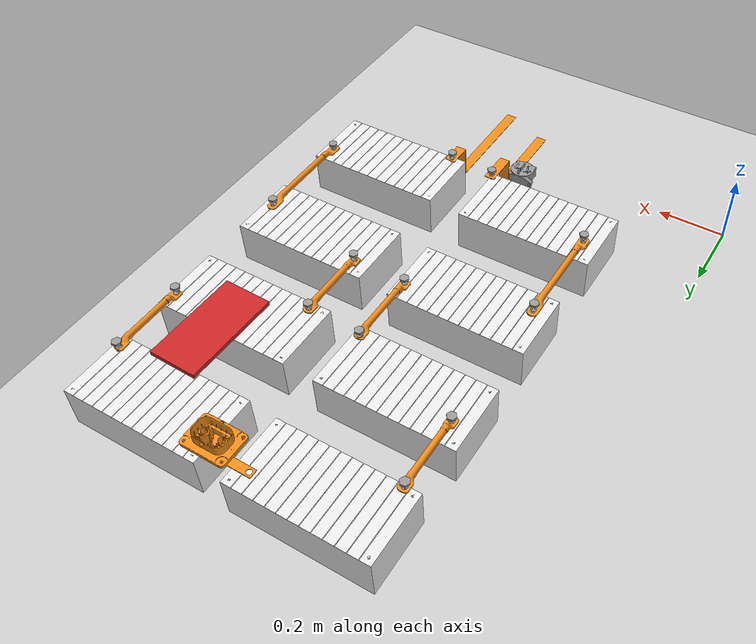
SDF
<sdf version="1.6">
 <world name="Pack6">
  <light name="sun" type="directional">
   <pose>0 0 10 0 -0 0</pose>
   <diffuse>0.8 0.8 0.8 1</diffuse>
   <specular>0.1 0.1 0.1 1</specular>
   <attenuation>
    <range>1000</range>
    <constant>0.9</constant>
    <linear>0.01</linear>
    <quadratic>0.001</quadratic>
   </attenuation>
   <direction>-0.5 0.5 -1</direction>
  </light>
  <model name="ground_plane">
   <static>1</static>
   <link name="link">
    <collision name="collision">
     <geometry><plane><normal>0 0 1</normal><size>100 100</size></plane></geometry>
     <surface><friction><ode><mu>100</mu><mu2>50</mu2></ode></friction></surface>
    </collision>
    <visual name="visual">
     <cast_shadows>0</cast_shadows>
     <geometry><plane><normal>0 0 1</normal><size>100 100</size></plane></geometry>
     <material>
      <script><uri>file://media/materials/scripts/gazebo.material</uri><name>Gazebo/Grey</name></script>
     </material>
    </visual>
   </link>
  </model>
  <model name="HW_battery_module_sc_fr_half">
   <link name="link_1">
    <inertial>
     <mass>10</mass>
     <inertia><ixx>0.1275</ixx><ixy>0</ixy><ixz>0</ixz><iyy>0.3997</iyy><iyz>0</iyz><izz>0.4538</izz></inertia>
    </inertial>
    <visual name="visual">
     <geometry>
      <mesh>
       <uri>/home/wanghu26/battery_ws/src/battery_model/battery_model_stl/HW_Battery Module.stl</uri>
       <scale>0.5 0.5 0.5</scale>
      </mesh>
     </geometry>
     <material>
      <lighting>1</lighting>
      <script><uri>file://media/materials/scripts/gazebo.material</uri><name>Gazebo/White</name></script>
      <shader type="pixel"/>
     </material>
    </visual>
    <collision name="collision">
     <geometry><box><size>0.33 0.165 0.105</size></box></geometry>
     <surface>
      <friction>
       <ode><mu>1</mu><mu2>1</mu2><fdir1>0 0 0</fdir1><slip1>0</slip1><slip2>0</slip2></ode>
       <torsional>
        <coefficient>1</coefficient>
        <patch_radius>0</patch_radius>
        <surface_radius>0</surface_radius>
        <use_patch_radius>1</use_patch_radius>
        <ode><slip>0</slip></ode>
       </torsional>
      </friction>
      <bounce><restitution_coefficient>0</restitution_coefficient><threshold>1e+06</threshold></bounce>
      <contact>
       <collide_without_contact>0</collide_without_contact>
       <collide_without_contact_bitmask>1</collide_without_contact_bitmask>
       <collide_bitmask>1</collide_bitmask>
       <ode>
        <soft_cfm>0</soft_cfm>
        <soft_erp>0.2</soft_erp>
        <kp>1e+13</kp>
        <kd>1</kd>
        <max_vel>0.01</max_vel>
        <min_depth>0.0001</min_depth>
       </ode>
       <bullet>
        <split_impulse>1</split_impulse>
        <split_impulse_penetration_threshold>-0.01</split_impulse_penetration_threshold>
        <soft_cfm>0</soft_cfm>
        <soft_erp>0.2</soft_erp>
        <kp>1e+13</kp>
        <kd>1</kd>
       </bullet>
      </contact>
     </surface>
    </collision>
   </link>
   <static>1</static>
   <pose>0.299993 0.656978 0.4 0 -0 0</pose>
  </model>
  <model name="HW_battery_module_sc_fr_1_half">
   <link name="link_1">
    <inertial>
     <mass>10</mass>
     <inertia><ixx>0.1275</ixx><ixy>0</ixy><ixz>0</ixz><iyy>0.3997</iyy><iyz>0</iyz><izz>0.4538</izz></inertia>
    </inertial>
    <visual name="visual">
     <geometry>
      <mesh>
       <uri>/home/wanghu26/battery_ws/src/battery_model/battery_model_stl/HW_Battery Module.stl</uri>
       <scale>0.5 0.5 0.5</scale>
      </mesh>
     </geometry>
     <material>
      <lighting>1</lighting>
      <script><uri>file://media/materials/scripts/gazebo.material</uri><name>Gazebo/White</name></script>
      <shader type="pixel"/>
     </material>
    </visual>
    <collision name="collision">
     <geometry><box><size>0.33 0.165 0.105</size></box></geometry>
     <surface>
      <friction>
       <ode><mu>1</mu><mu2>1</mu2><fdir1>0 0 0</fdir1><slip1>0</slip1><slip2>0</slip2></ode>
       <torsional>
        <coefficient>1</coefficient>
        <patch_radius>0</patch_radius>
        <surface_radius>0</surface_radius>
        <use_patch_radius>1</use_patch_radius>
        <ode><slip>0</slip></ode>
       </torsional>
      </friction>
      <bounce><restitution_coefficient>0</restitution_coefficient><threshold>1e+06</threshold></bounce>
      <contact>
       <collide_without_contact>0</collide_without_contact>
       <collide_without_contact_bitmask>1</collide_without_contact_bitmask>
       <collide_bitmask>1</collide_bitmask>
       <ode>
        <soft_cfm>0</soft_cfm>
        <soft_erp>0.2</soft_erp>
        <kp>1e+13</kp>
        <kd>1</kd>
        <max_vel>0.01</max_vel>
        <min_depth>0.0001</min_depth>
       </ode>
       <bullet>
        <split_impulse>1</split_impulse>
        <split_impulse_penetration_threshold>-0.01</split_impulse_penetration_threshold>
        <soft_cfm>0</soft_cfm>
        <soft_erp>0.2</soft_erp>
        <kp>1e+13</kp>
        <kd>1</kd>
       </bullet>
      </contact>
     </surface>
    </collision>
   </link>
   <static>1</static>
   <pose>0.303126 0.953183 0.4 0 -0 0</pose>
  </model>
  <model name="HW_battery_module_sc_fr_2_half">
   <link name="link_1">
    <inertial>
     <mass>10</mass>
     <inertia><ixx>0.1275</ixx><ixy>0</ixy><ixz>0</ixz><iyy>0.3997</iyy><iyz>0</iyz><izz>0.4538</izz></inertia>
    </inertial>
    <visual name="visual">
     <geometry>
      <mesh>
       <uri>/home/wanghu26/battery_ws/src/battery_model/battery_model_stl/HW_Battery Module.stl</uri>
       <scale>0.5 0.5 0.5</scale>
      </mesh>
     </geometry>
     <material>
      <lighting>1</lighting>
      <script><uri>file://media/materials/scripts/gazebo.material</uri><name>Gazebo/White</name></script>
      <shader type="pixel"/>
     </material>
    </visual>
    <collision name="collision">
     <geometry><box><size>0.33 0.165 0.105</size></box></geometry>
     <surface>
      <friction>
       <ode><mu>1</mu><mu2>1</mu2><fdir1>0 0 0</fdir1><slip1>0</slip1><slip2>0</slip2></ode>
       <torsional>
        <coefficient>1</coefficient>
        <patch_radius>0</patch_radius>
        <surface_radius>0</surface_radius>
        <use_patch_radius>1</use_patch_radius>
        <ode><slip>0</slip></ode>
       </torsional>
      </friction>
      <bounce><restitution_coefficient>0</restitution_coefficient><threshold>1e+06</threshold></bounce>
      <contact>
       <collide_without_contact>0</collide_without_contact>
       <collide_without_contact_bitmask>1</collide_without_contact_bitmask>
       <collide_bitmask>1</collide_bitmask>
       <ode>
        <soft_cfm>0</soft_cfm>
        <soft_erp>0.2</soft_erp>
        <kp>1e+13</kp>
        <kd>1</kd>
        <max_vel>0.01</max_vel>
        <min_depth>0.0001</min_depth>
       </ode>
       <bullet>
        <split_impulse>1</split_impulse>
        <split_impulse_penetration_threshold>-0.01</split_impulse_penetration_threshold>
        <soft_cfm>0</soft_cfm>
        <soft_erp>0.2</soft_erp>
        <kp>1e+13</kp>
        <kd>1</kd>
       </bullet>
      </contact>
     </surface>
    </collision>
   </link>
   <static>1</static>
   <pose>0.71 0.945576 0.4 0 -0 0</pose>
  </model>
  <model name="HW_battery_module_sc_fr_3_half">
   <link name="link_1">
    <inertial>
     <mass>10</mass>
     <inertia><ixx>0.1275</ixx><ixy>0</ixy><ixz>0</ixz><iyy>0.3997</iyy><iyz>0</iyz><izz>0.4538</izz></inertia>
    </inertial>
    <visual name="visual">
     <geometry>
      <mesh>
       <uri>/home/wanghu26/battery_ws/src/battery_model/battery_model_stl/HW_Battery Module.stl</uri>
       <scale>0.5 0.5 0.5</scale>
      </mesh>
     </geometry>
     <material>
      <lighting>1</lighting>
      <script><uri>file://media/materials/scripts/gazebo.material</uri><name>Gazebo/White</name></script>
      <shader type="pixel"/>
     </material>
    </visual>
    <collision name="collision">
     <geometry><box><size>0.33 0.165 0.105</size></box></geometry>
     <surface>
      <friction>
       <ode><mu>1</mu><mu2>1</mu2><fdir1>0 0 0</fdir1><slip1>0</slip1><slip2>0</slip2></ode>
       <torsional>
        <coefficient>1</coefficient>
        <patch_radius>0</patch_radius>
        <surface_radius>0</surface_radius>
        <use_patch_radius>1</use_patch_radius>
        <ode><slip>0</slip></ode>
       </torsional>
      </friction>
      <bounce><restitution_coefficient>0</restitution_coefficient><threshold>1e+06</threshold></bounce>
      <contact>
       <collide_without_contact>0</collide_without_contact>
       <collide_without_contact_bitmask>1</collide_without_contact_bitmask>
       <collide_bitmask>1</collide_bitmask>
       <ode>
        <soft_cfm>0</soft_cfm>
        <soft_erp>0.2</soft_erp>
        <kp>1e+13</kp>
        <kd>1</kd>
        <max_vel>0.01</max_vel>
        <min_depth>0.0001</min_depth>
       </ode>
       <bullet>
        <split_impulse>1</split_impulse>
        <split_impulse_penetration_threshold>-0.01</split_impulse_penetration_threshold>
        <soft_cfm>0</soft_cfm>
        <soft_erp>0.2</soft_erp>
        <kp>1e+13</kp>
        <kd>1</kd>
       </bullet>
      </contact>
     </surface>
    </collision>
   </link>
   <static>1</static>
   <pose>0.71 0.651527 0.4 0 -0 0</pose>
  </model>
  <model name="HW_HV_cable_sc_f">
   <link name="link_1">
    <inertial>
     <mass>0.5</mass>
     <inertia><ixx>0.0017</ixx><ixy>0</ixy><ixz>0</ixz><iyy>0.00033333</iyy><iyz>0</iyz><izz>0.0017</izz></inertia>
    </inertial>
    <visual name="visual">
     <geometry>
      <mesh>
       <uri>/home/wanghu26/battery_ws/src/battery_model/battery_model_stl/HW_HV_cable .stl</uri>
       <scale>1 1 1</scale>
      </mesh>
     </geometry>
     <material>
      <lighting>1</lighting>
      <script><uri>file://media/materials/scripts/gazebo.material</uri><name>Gazebo/Orange</name></script>
      <shader type="pixel"/>
     </material>
    </visual>
    <collision name="collision">
     <pose>0.2 0 0 0 -0 0</pose>
     <geometry><box><size>0.02 0.15 0.02</size></box></geometry>
     <surface>
      <friction>
       <ode><mu>1</mu><mu2>1</mu2><fdir1>0 0 0</fdir1><slip1>0</slip1><slip2>0</slip2></ode>
       <torsional>
        <coefficient>1</coefficient>
        <patch_radius>0</patch_radius>
        <surface_radius>0</surface_radius>
        <use_patch_radius>1</use_patch_radius>
        <ode><slip>0</slip></ode>
       </torsional>
      </friction>
      <bounce><restitution_coefficient>0</restitution_coefficient><threshold>1e+06</threshold></bounce>
      <contact>
       <collide_without_contact>0</collide_without_contact>
       <collide_without_contact_bitmask>1</collide_without_contact_bitmask>
       <collide_bitmask>1</collide_bitmask>
       <ode>
        <soft_cfm>0</soft_cfm>
        <soft_erp>0.2</soft_erp>
        <kp>1e+13</kp>
        <kd>1</kd>
        <max_vel>0.01</max_vel>
        <min_depth>0</min_depth>
       </ode>
       <bullet>
        <split_impulse>1</split_impulse>
        <split_impulse_penetration_threshold>-0.01</split_impulse_penetration_threshold>
        <soft_cfm>0</soft_cfm>
        <soft_erp>0.2</soft_erp>
        <kp>1e+13</kp>
        <kd>1</kd>
       </bullet>
      </contact>
     </surface>
    </collision>
   </link>
   <static>1</static>
   <plugin name="groun_truth" filename="libgazebo_ros_p3d.so">
    <frameName>map</frameName>
    <bodyName>link_1</bodyName>
    <topicName>odom0a</topicName>
    <updateRate>30.0</updateRate>
   </plugin>
   <pose>0.17 0.811992 0.47 0 -0 0</pose>
  </model>
  <model name="HW_HV_cable_sc_f_1">
   <link name="link_1">
    <inertial>
     <mass>0.5</mass>
     <inertia><ixx>0.0017</ixx><ixy>0</ixy><ixz>0</ixz><iyy>0.00033333</iyy><iyz>0</iyz><izz>0.0017</izz></inertia>
    </inertial>
    <visual name="visual">
     <geometry>
      <mesh>
       <uri>/home/wanghu26/battery_ws/src/battery_model/battery_model_stl/HW_HV_cable .stl</uri>
       <scale>1 1 1</scale>
      </mesh>
     </geometry>
     <material>
      <lighting>1</lighting>
      <script><uri>file://media/materials/scripts/gazebo.material</uri><name>Gazebo/Orange</name></script>
      <shader type="pixel"/>
     </material>
    </visual>
    <collision name="collision">
     <pose>0.1 0 0 0 -0 0</pose>
     <geometry><box><size>0.02 0.2 0.02</size></box></geometry>
     <surface>
      <friction>
       <ode><mu>1</mu><mu2>1</mu2><fdir1>0 0 0</fdir1><slip1>0</slip1><slip2>0</slip2></ode>
       <torsional>
        <coefficient>1</coefficient>
        <patch_radius>0</patch_radius>
        <surface_radius>0</surface_radius>
        <use_patch_radius>1</use_patch_radius>
        <ode><slip>0</slip></ode>
       </torsional>
      </friction>
      <bounce><restitution_coefficient>0</restitution_coefficient><threshold>1e+06</threshold></bounce>
      <contact>
       <collide_without_contact>0</collide_without_contact>
       <collide_without_contact_bitmask>1</collide_without_contact_bitmask>
       <collide_bitmask>1</collide_bitmask>
       <ode>
        <soft_cfm>0</soft_cfm>
        <soft_erp>0.2</soft_erp>
        <kp>1e+13</kp>
        <kd>1</kd>
        <max_vel>0.01</max_vel>
        <min_depth>0</min_depth>
       </ode>
       <bullet>
        <split_impulse>1</split_impulse>
        <split_impulse_penetration_threshold>-0.01</split_impulse_penetration_threshold>
        <soft_cfm>0</soft_cfm>
        <soft_erp>0.2</soft_erp>
        <kp>1e+13</kp>
        <kd>1</kd>
       </bullet>
      </contact>
     </surface>
    </collision>
   </link>
   <static>1</static>
   <plugin name="groun_truth" filename="libgazebo_ros_p3d.so">
    <frameName>map</frameName>
    <bodyName>link_1</bodyName>
    <topicName>odom1a</topicName>
    <updateRate>30.0</updateRate>
   </plugin>
   <pose>0.85 0.814118 0.458817 0 -0 0</pose>
  </model>
  <model name="HW_tap_bolt_sc_f_0">
   <link name="link_2">
    <inertial>
     <mass>1</mass>
     <inertia>
      <ixx>0.0166667</ixx>
      <ixy>0</ixy>
      <ixz>0</ixz>
      <iyy>0.0166667</iyy>
      <iyz>0</iyz>
      <izz>0.0166667</izz>
     </inertia>
    </inertial>
    <pose>0 0 -1e-06 3.14159 -0.002979 3.14159</pose>
    <visual name="visual">
     <geometry>
      <mesh>
       <uri>/home/wanghu26/battery_ws/src/battery_model/battery_model_stl/HW_hex_bolt_tap_thread.stl</uri>
       <scale>1 1 1</scale>
      </mesh>
     </geometry>
     <material>
      <lighting>1</lighting>
      <script><uri>file://media/materials/scripts/gazebo.material</uri><name>Gazebo/Grey</name></script>
      <shader type="pixel"/>
     </material>
    </visual>
    <collision name="collision">
     <pose>0 -0.1 0 0 -0 0</pose>
     <geometry><box><size>0.02 0.02 0.04</size></box></geometry>
     <surface>
      <friction>
       <ode><mu>1</mu><mu2>1</mu2><fdir1>0 0 0</fdir1><slip1>0</slip1><slip2>0</slip2></ode>
       <torsional>
        <coefficient>1</coefficient>
        <patch_radius>0.1</patch_radius>
        <surface_radius>0.1</surface_radius>
        <use_patch_radius>1</use_patch_radius>
        <ode><slip>0</slip></ode>
       </torsional>
      </friction>
      <bounce><restitution_coefficient>0</restitution_coefficient><threshold>1e+06</threshold></bounce>
      <contact>
       <collide_without_contact>0</collide_without_contact>
       <collide_without_contact_bitmask>1</collide_without_contact_bitmask>
       <collide_bitmask>1</collide_bitmask>
       <ode>
        <soft_cfm>0</soft_cfm>
        <soft_erp>0.2</soft_erp>
        <kp>1e+13</kp>
        <kd>1</kd>
        <max_vel>0.01</max_vel>
        <min_depth>0</min_depth>
       </ode>
       <bullet>
        <split_impulse>1</split_impulse>
        <split_impulse_penetration_threshold>-0.01</split_impulse_penetration_threshold>
        <soft_cfm>0</soft_cfm>
        <soft_erp>0.2</soft_erp>
        <kp>1e+13</kp>
        <kd>1</kd>
       </bullet>
      </contact>
     </surface>
    </collision>
   </link>
   <static>1</static>
   <pose>0.454463 0.600151 0.47 0 -0 0</pose>
  </model>
  <model name="HW_tap_bolt_sc_f_1">
   <link name="link_2">
    <inertial>
     <mass>1</mass>
     <inertia>
      <ixx>0.0166667</ixx>
      <ixy>0</ixy>
      <ixz>0</ixz>
      <iyy>0.0166667</iyy>
      <iyz>0</iyz>
      <izz>0.0166667</izz>
     </inertia>
    </inertial>
    <pose>0 0 -1e-06 3.14159 -0.002979 3.14159</pose>
    <visual name="visual">
     <geometry>
      <mesh>
       <uri>/home/wanghu26/battery_ws/src/battery_model/battery_model_stl/HW_hex_bolt_tap_thread.stl</uri>
       <scale>1 1 1</scale>
      </mesh>
     </geometry>
     <material>
      <lighting>1</lighting>
      <script><uri>file://media/materials/scripts/gazebo.material</uri><name>Gazebo/Grey</name></script>
      <shader type="pixel"/>
     </material>
    </visual>
    <collision name="collision">
     <pose>0 0.1 0 0 -0 0</pose>
     <geometry><box><size>0.02 0.02 0.04</size></box></geometry>
     <surface>
      <friction>
       <ode><mu>1</mu><mu2>1</mu2><fdir1>0 0 0</fdir1><slip1>0</slip1><slip2>0</slip2></ode>
       <torsional>
        <coefficient>1</coefficient>
        <patch_radius>0.1</patch_radius>
        <surface_radius>0.1</surface_radius>
        <use_patch_radius>1</use_patch_radius>
        <ode><slip>0</slip></ode>
       </torsional>
      </friction>
      <bounce><restitution_coefficient>0</restitution_coefficient><threshold>1e+06</threshold></bounce>
      <contact>
       <collide_without_contact>0</collide_without_contact>
       <collide_without_contact_bitmask>1</collide_without_contact_bitmask>
       <collide_bitmask>1</collide_bitmask>
       <ode>
        <soft_cfm>0</soft_cfm>
        <soft_erp>0.2</soft_erp>
        <kp>1e+13</kp>
        <kd>1</kd>
        <max_vel>0.01</max_vel>
        <min_depth>0</min_depth>
       </ode>
       <bullet>
        <split_impulse>1</split_impulse>
        <split_impulse_penetration_threshold>-0.01</split_impulse_penetration_threshold>
        <soft_cfm>0</soft_cfm>
        <soft_erp>0.2</soft_erp>
        <kp>1e+13</kp>
        <kd>1</kd>
       </bullet>
      </contact>
     </surface>
    </collision>
   </link>
   <static>1</static>
   <pose>0.17 0.690805 0.47 0 -0 0</pose>
  </model>
  <model name="HW_tap_bolt_sc_f_2">
   <link name="link_2">
    <inertial>
     <mass>1</mass>
     <inertia>
      <ixx>0.0166667</ixx>
      <ixy>0</ixy>
      <ixz>0</ixz>
      <iyy>0.0166667</iyy>
      <iyz>0</iyz>
      <izz>0.0166667</izz>
     </inertia>
    </inertial>
    <pose>0 0 -1e-06 3.14159 -0.002979 3.14159</pose>
    <visual name="visual">
     <geometry>
      <mesh>
       <uri>/home/wanghu26/battery_ws/src/battery_model/battery_model_stl/HW_hex_bolt_tap_thread.stl</uri>
       <scale>1 1 1</scale>
      </mesh>
     </geometry>
     <material>
      <lighting>1</lighting>
      <script><uri>file://media/materials/scripts/gazebo.material</uri><name>Gazebo/Grey</name></script>
      <shader type="pixel"/>
     </material>
    </visual>
    <collision name="collision">
     <pose>0 0.1 0 0 -0 0</pose>
     <geometry><box><size>0.02 0.02 0.04</size></box></geometry>
     <surface>
      <friction>
       <ode><mu>1</mu><mu2>1</mu2><fdir1>0 0 0</fdir1><slip1>0</slip1><slip2>0</slip2></ode>
       <torsional>
        <coefficient>1</coefficient>
        <patch_radius>0.1</patch_radius>
        <surface_radius>0.1</surface_radius>
        <use_patch_radius>1</use_patch_radius>
        <ode><slip>0</slip></ode>
       </torsional>
      </friction>
      <bounce><restitution_coefficient>0</restitution_coefficient><threshold>1e+06</threshold></bounce>
      <contact>
       <collide_without_contact>0</collide_without_contact>
       <collide_without_contact_bitmask>1</collide_without_contact_bitmask>
       <collide_bitmask>1</collide_bitmask>
       <ode>
        <soft_cfm>0</soft_cfm>
        <soft_erp>0.2</soft_erp>
        <kp>1e+13</kp>
        <kd>1</kd>
        <max_vel>0.01</max_vel>
        <min_depth>0</min_depth>
       </ode>
       <bullet>
        <split_impulse>1</split_impulse>
        <split_impulse_penetration_threshold>-0.01</split_impulse_penetration_threshold>
        <soft_cfm>0</soft_cfm>
        <soft_erp>0.2</soft_erp>
        <kp>1e+13</kp>
        <kd>1</kd>
       </bullet>
      </contact>
     </surface>
    </collision>
   </link>
   <static>1</static>
   <pose>0.17 0.930276 0.47 0 -0 0</pose>
  </model>
  <model name="HW_tap_bolt_sc_f_3">
   <link name="link_2">
    <inertial>
     <mass>1</mass>
     <inertia>
      <ixx>0.0166667</ixx>
      <ixy>0</ixy>
      <ixz>0</ixz>
      <iyy>0.0166667</iyy>
      <iyz>0</iyz>
      <izz>0.0166667</izz>
     </inertia>
    </inertial>
    <pose>0 0 -1e-06 3.14159 -0.002979 3.14159</pose>
    <visual name="visual">
     <geometry>
      <mesh>
       <uri>/home/wanghu26/battery_ws/src/battery_model/battery_model_stl/HW_hex_bolt_tap_thread.stl</uri>
       <scale>1 1 1</scale>
      </mesh>
     </geometry>
     <material>
      <lighting>1</lighting>
      <script><uri>file://media/materials/scripts/gazebo.material</uri><name>Gazebo/Grey</name></script>
      <shader type="pixel"/>
     </material>
    </visual>
    <collision name="collision">
     <pose>0 0.1 0 0 -0 0</pose>
     <geometry><box><size>0.02 0.02 0.04</size></box></geometry>
     <surface>
      <friction>
       <ode><mu>1</mu><mu2>1</mu2><fdir1>0 0 0</fdir1><slip1>0</slip1><slip2>0</slip2></ode>
       <torsional>
        <coefficient>1</coefficient>
        <patch_radius>0.1</patch_radius>
        <surface_radius>0.1</surface_radius>
        <use_patch_radius>1</use_patch_radius>
        <ode><slip>0</slip></ode>
       </torsional>
      </friction>
      <bounce><restitution_coefficient>0</restitution_coefficient><threshold>1e+06</threshold></bounce>
      <contact>
       <collide_without_contact>0</collide_without_contact>
       <collide_without_contact_bitmask>1</collide_without_contact_bitmask>
       <collide_bitmask>1</collide_bitmask>
       <ode>
        <soft_cfm>0</soft_cfm>
        <soft_erp>0.2</soft_erp>
        <kp>1e+13</kp>
        <kd>1</kd>
        <max_vel>0.01</max_vel>
        <min_depth>0</min_depth>
       </ode>
       <bullet>
        <split_impulse>1</split_impulse>
        <split_impulse_penetration_threshold>-0.01</split_impulse_penetration_threshold>
        <soft_cfm>0</soft_cfm>
        <soft_erp>0.2</soft_erp>
        <kp>1e+13</kp>
        <kd>1</kd>
       </bullet>
      </contact>
     </surface>
    </collision>
   </link>
   <static>1</static>
   <pose>0.85 0.933431 0.455628 0 -0 0</pose>
  </model>
  <model name="HW_tap_bolt_sc_f_4">
   <link name="link_2">
    <inertial>
     <mass>1</mass>
     <inertia>
      <ixx>0.0166667</ixx>
      <ixy>0</ixy>
      <ixz>0</ixz>
      <iyy>0.0166667</iyy>
      <iyz>0</iyz>
      <izz>0.0166667</izz>
     </inertia>
    </inertial>
    <pose>0 0 -1e-06 3.14159 -0.002979 3.14159</pose>
    <visual name="visual">
     <geometry>
      <mesh>
       <uri>/home/wanghu26/battery_ws/src/battery_model/battery_model_stl/HW_hex_bolt_tap_thread.stl</uri>
       <scale>1 1 1</scale>
      </mesh>
     </geometry>
     <material>
      <lighting>1</lighting>
      <script><uri>file://media/materials/scripts/gazebo.material</uri><name>Gazebo/Grey</name></script>
      <shader type="pixel"/>
     </material>
    </visual>
    <collision name="collision">
     <pose>0 0.1 0 0 -0 0</pose>
     <geometry><box><size>0.02 0.02 0.04</size></box></geometry>
     <surface>
      <friction>
       <ode><mu>1</mu><mu2>1</mu2><fdir1>0 0 0</fdir1><slip1>0</slip1><slip2>0</slip2></ode>
       <torsional>
        <coefficient>1</coefficient>
        <patch_radius>0.1</patch_radius>
        <surface_radius>0.1</surface_radius>
        <use_patch_radius>1</use_patch_radius>
        <ode><slip>0</slip></ode>
       </torsional>
      </friction>
      <bounce><restitution_coefficient>0</restitution_coefficient><threshold>1e+06</threshold></bounce>
      <contact>
       <collide_without_contact>0</collide_without_contact>
       <collide_without_contact_bitmask>1</collide_without_contact_bitmask>
       <collide_bitmask>1</collide_bitmask>
       <ode>
        <soft_cfm>0</soft_cfm>
        <soft_erp>0.2</soft_erp>
        <kp>1e+13</kp>
        <kd>1</kd>
        <max_vel>0.01</max_vel>
        <min_depth>0</min_depth>
       </ode>
       <bullet>
        <split_impulse>1</split_impulse>
        <split_impulse_penetration_threshold>-0.01</split_impulse_penetration_threshold>
        <soft_cfm>0</soft_cfm>
        <soft_erp>0.2</soft_erp>
        <kp>1e+13</kp>
        <kd>1</kd>
       </bullet>
      </contact>
     </surface>
    </collision>
   </link>
   <static>1</static>
   <pose>0.85 0.69367 0.453535 0 -0 0</pose>
  </model>
  <model name="HW_tap_bolt_sc_f_5">
   <link name="link_2">
    <inertial>
     <mass>1</mass>
     <inertia>
      <ixx>0.0166667</ixx>
      <ixy>0</ixy>
      <ixz>0</ixz>
      <iyy>0.0166667</iyy>
      <iyz>0</iyz>
      <izz>0.0166667</izz>
     </inertia>
    </inertial>
    <pose>0 0 -1e-06 3.14159 -0.002979 3.14159</pose>
    <visual name="visual">
     <geometry>
      <mesh>
       <uri>/home/wanghu26/battery_ws/src/battery_model/battery_model_stl/HW_hex_bolt_tap_thread.stl</uri>
       <scale>1 1 1</scale>
      </mesh>
     </geometry>
     <material>
      <lighting>1</lighting>
      <script><uri>file://media/materials/scripts/gazebo.material</uri><name>Gazebo/Grey</name></script>
      <shader type="pixel"/>
     </material>
    </visual>
    <collision name="collision">
     <pose>0 -0.1 0 0 -0 0</pose>
     <geometry><box><size>0.02 0.02 0.04</size></box></geometry>
     <surface>
      <friction>
       <ode><mu>1</mu><mu2>1</mu2><fdir1>0 0 0</fdir1><slip1>0</slip1><slip2>0</slip2></ode>
       <torsional>
        <coefficient>1</coefficient>
        <patch_radius>0.1</patch_radius>
        <surface_radius>0.1</surface_radius>
        <use_patch_radius>1</use_patch_radius>
        <ode><slip>0</slip></ode>
       </torsional>
      </friction>
      <bounce><restitution_coefficient>0</restitution_coefficient><threshold>1e+06</threshold></bounce>
      <contact>
       <collide_without_contact>0</collide_without_contact>
       <collide_without_contact_bitmask>1</collide_without_contact_bitmask>
       <collide_bitmask>1</collide_bitmask>
       <ode>
        <soft_cfm>0</soft_cfm>
        <soft_erp>0.2</soft_erp>
        <kp>1e+13</kp>
        <kd>1</kd>
        <max_vel>0.01</max_vel>
        <min_depth>0</min_depth>
       </ode>
       <bullet>
        <split_impulse>1</split_impulse>
        <split_impulse_penetration_threshold>-0.01</split_impulse_penetration_threshold>
        <soft_cfm>0</soft_cfm>
        <soft_erp>0.2</soft_erp>
        <kp>1e+13</kp>
        <kd>1</kd>
       </bullet>
      </contact>
     </surface>
    </collision>
   </link>
   <static>1</static>
   <pose>0.568 0.592208 0.47 0 -0 0</pose>
  </model>
  <model name="Contactor">
   <link name="link_1">
    <pose>0 -0 -0 1.60329 -0 0</pose>
    <inertial>
     <mass>1</mass>
     <inertia>
      <ixx>0.166667</ixx>
      <ixy>0</ixy>
      <ixz>0</ixz>
      <iyy>0.166667</iyy>
      <iyz>0</iyz>
      <izz>0.166667</izz>
     </inertia>
    </inertial>
    <visual name="visual">
     <geometry>
      <mesh>
       <uri>/home/wanghu26/battery_ws/src/battery_model/battery_model_stl/HW_Tyco KiloVac EV200 Contactor Side Mount.stl</uri>
       <scale>1 1 1</scale>
      </mesh>
     </geometry>
     <material>
      <lighting>1</lighting>
      <script><uri>file://media/materials/scripts/gazebo.material</uri><name>Gazebo/Grey</name></script>
     </material>
    </visual>
    <collision name="collision">
     <geometry>
      <mesh>
       <uri>/home/wanghu26/battery_ws/src/battery_model/battery_model_stl/HW_Tyco KiloVac EV200 Contactor Side Mount.stl</uri>
      </mesh>
     </geometry>
     <surface>
      <friction>
       <ode><mu>1</mu><mu2>1</mu2><fdir1>0 0 0</fdir1><slip1>0</slip1><slip2>0</slip2></ode>
       <torsional>
        <coefficient>1</coefficient>
        <patch_radius>0</patch_radius>
        <surface_radius>0</surface_radius>
        <use_patch_radius>1</use_patch_radius>
        <ode><slip>0</slip></ode>
       </torsional>
      </friction>
      <bounce><restitution_coefficient>0</restitution_coefficient><threshold>1e+06</threshold></bounce>
      <contact>
       <collide_without_contact>0</collide_without_contact>
       <collide_without_contact_bitmask>1</collide_without_contact_bitmask>
       <collide_bitmask>1</collide_bitmask>
       <ode>
        <soft_cfm>0</soft_cfm>
        <soft_erp>0.2</soft_erp>
        <kp>1e+13</kp>
        <kd>1</kd>
        <max_vel>0.01</max_vel>
        <min_depth>0</min_depth>
       </ode>
       <bullet>
        <split_impulse>1</split_impulse>
        <split_impulse_penetration_threshold>-0.01</split_impulse_penetration_threshold>
        <soft_cfm>0</soft_cfm>
        <soft_erp>0.2</soft_erp>
        <kp>1e+13</kp>
        <kd>1</kd>
       </bullet>
      </contact>
     </surface>
    </collision>
   </link>
   <static>1</static>
   <pose>0.443 0.489128 0.4 0 -0 0</pose>
  </model>
  <model name="bus_neg">
   <link name="link_3">
    <pose>-0 0 -0 1.57326 -0 0</pose>
    <inertial>
     <mass>1</mass>
     <inertia>
      <ixx>0.166667</ixx>
      <ixy>0</ixy>
      <ixz>0</ixz>
      <iyy>0.166667</iyy>
      <iyz>0</iyz>
      <izz>0.166667</izz>
     </inertia>
    </inertial>
    <visual name="visual">
     <geometry>
      <mesh>
       <uri>/home/wanghu26/battery_ws/src/battery_model/battery_model_stl/HW_bus_bar_neg.stl</uri>
       <scale>1 0.5 0.7</scale>
      </mesh>
     </geometry>
     <material>
      <lighting>1</lighting>
      <script><uri>file://media/materials/scripts/gazebo.material</uri><name>Gazebo/Orange</name></script>
     </material>
    </visual>
    <collision name="collision">
     <pose>0 0 0.1 0 -0 0</pose>
     <geometry>
      <mesh><uri>/home/wanghu26/battery_ws/src/battery_model/battery_model_stl/HW_bus_bar_neg.stl</uri></mesh>
     </geometry>
     <surface>
      <friction>
       <ode><mu>1</mu><mu2>1</mu2><fdir1>0 0 0</fdir1><slip1>0</slip1><slip2>0</slip2></ode>
       <torsional>
        <coefficient>1</coefficient>
        <patch_radius>0</patch_radius>
        <surface_radius>0</surface_radius>
        <use_patch_radius>1</use_patch_radius>
        <ode><slip>0</slip></ode>
       </torsional>
      </friction>
      <bounce><restitution_coefficient>0</restitution_coefficient><threshold>1e+06</threshold></bounce>
      <contact>
       <collide_without_contact>0</collide_without_contact>
       <collide_without_contact_bitmask>1</collide_without_contact_bitmask>
       <collide_bitmask>1</collide_bitmask>
       <ode>
        <soft_cfm>0</soft_cfm>
        <soft_erp>0.2</soft_erp>
        <kp>1e+13</kp>
        <kd>1</kd>
        <max_vel>0.01</max_vel>
        <min_depth>0</min_depth>
       </ode>
       <bullet>
        <split_impulse>1</split_impulse>
        <split_impulse_penetration_threshold>-0.01</split_impulse_penetration_threshold>
        <soft_cfm>0</soft_cfm>
        <soft_erp>0.2</soft_erp>
        <kp>1e+13</kp>
        <kd>1</kd>
       </bullet>
      </contact>
     </surface>
    </collision>
   </link>
   <static>1</static>
   <pose>0.555 0.604483 0.47 0 -0 0</pose>
  </model>
  <model name="bus_pos">
   <link name="link_5">
    <pose>0 0 -0 1.56922 -0 0</pose>
    <inertial>
     <mass>1</mass>
     <inertia>
      <ixx>0.166667</ixx>
      <ixy>0</ixy>
      <ixz>0</ixz>
      <iyy>0.166667</iyy>
      <iyz>0</iyz>
      <izz>0.166667</izz>
     </inertia>
    </inertial>
    <visual name="visual">
     <geometry>
      <mesh>
       <uri>/home/wanghu26/battery_ws/src/battery_model/battery_model_stl/HW_bus_bar_pos.stl</uri>
       <scale>1 0.5 1</scale>
      </mesh>
     </geometry>
     <material>
      <lighting>1</lighting>
      <script><uri>file://media/materials/scripts/gazebo.material</uri><name>Gazebo/Orange</name></script>
     </material>
    </visual>
    <collision name="collision">
     <pose>0 0 0.1 0 -0 0</pose>
     <geometry>
      <mesh><uri>/home/wanghu26/battery_ws/src/battery_model/battery_model_stl/HW_bus_bar_pos.stl</uri></mesh>
     </geometry>
     <surface>
      <friction>
       <ode><mu>1</mu><mu2>1</mu2><fdir1>0 0 0</fdir1><slip1>0</slip1><slip2>0</slip2></ode>
       <torsional>
        <coefficient>1</coefficient>
        <patch_radius>0</patch_radius>
        <surface_radius>0</surface_radius>
        <use_patch_radius>1</use_patch_radius>
        <ode><slip>0</slip></ode>
       </torsional>
      </friction>
      <bounce><restitution_coefficient>0</restitution_coefficient><threshold>1e+06</threshold></bounce>
      <contact>
       <collide_without_contact>0</collide_without_contact>
       <collide_without_contact_bitmask>1</collide_without_contact_bitmask>
       <collide_bitmask>1</collide_bitmask>
       <ode>
        <soft_cfm>0</soft_cfm>
        <soft_erp>0.2</soft_erp>
        <kp>1e+13</kp>
        <kd>1</kd>
        <max_vel>0.01</max_vel>
        <min_depth>0</min_depth>
       </ode>
       <bullet>
        <split_impulse>1</split_impulse>
        <split_impulse_penetration_threshold>-0.01</split_impulse_penetration_threshold>
        <soft_cfm>0</soft_cfm>
        <soft_erp>0.2</soft_erp>
        <kp>1e+13</kp>
        <kd>1</kd>
       </bullet>
      </contact>
     </surface>
    </collision>
   </link>
   <static>1</static>
   <pose>0.442 0.612866 0.47 0 -0 0</pose>
  </model>
  <model name="MSD">
   <link name="link_0">
    <inertial>
     <mass>1</mass>
     <inertia>
      <ixx>0.166667</ixx>
      <ixy>0</ixy>
      <ixz>0</ixz>
      <iyy>0.166667</iyy>
      <iyz>0</iyz>
      <izz>0.166667</izz>
     </inertia>
    </inertial>
    <visual name="visual">
     <geometry>
      <mesh>
       <uri>/home/wanghu26/battery_ws/src/battery_model/battery_model_stl/HW_MSD.stl</uri>
       <scale>1 1 1</scale>
      </mesh>
     </geometry>
     <material>
      <lighting>1</lighting>
      <script><uri>file://media/materials/scripts/gazebo.material</uri><name>Gazebo/Orange</name></script>
     </material>
    </visual>
    <collision name="collision">
     <geometry>
      <mesh><uri>/home/wanghu26/battery_ws/src/battery_model/battery_model_stl/HW_MSD.stl</uri></mesh>
     </geometry>
     <surface>
      <friction>
       <ode><mu>1</mu><mu2>1</mu2><fdir1>0 0 0</fdir1><slip1>0</slip1><slip2>0</slip2></ode>
       <torsional>
        <coefficient>1</coefficient>
        <patch_radius>0</patch_radius>
        <surface_radius>0</surface_radius>
        <use_patch_radius>1</use_patch_radius>
        <ode><slip>0</slip></ode>
       </torsional>
      </friction>
      <bounce><restitution_coefficient>0</restitution_coefficient><threshold>1e+06</threshold></bounce>
      <contact>
       <collide_without_contact>0</collide_without_contact>
       <collide_without_contact_bitmask>1</collide_without_contact_bitmask>
       <collide_bitmask>1</collide_bitmask>
       <ode>
        <soft_cfm>0</soft_cfm>
        <soft_erp>0.2</soft_erp>
        <kp>1e+13</kp>
        <kd>1</kd>
        <max_vel>0.01</max_vel>
        <min_depth>0</min_depth>
       </ode>
       <bullet>
        <split_impulse>1</split_impulse>
        <split_impulse_penetration_threshold>-0.01</split_impulse_penetration_threshold>
        <soft_cfm>0</soft_cfm>
        <soft_erp>0.2</soft_erp>
        <kp>1e+13</kp>
        <kd>1</kd>
       </bullet>
      </contact>
     </surface>
    </collision>
   </link>
   <static>1</static>
   <pose>0.496 1.54665 0.480899 0 -0 0</pose>
  </model>
  <gravity>0 0 -9.8</gravity>
  <magnetic_field>6e-06 2.3e-05 -4.2e-05</magnetic_field>
  <atmosphere type="adiabatic"/>
  <physics name="default_physics" default="0" type="ode">
   <max_step_size>0.001</max_step_size>
   <real_time_factor>1</real_time_factor>
   <real_time_update_rate>1000</real_time_update_rate>
  </physics>
  <scene><ambient>0.4 0.4 0.4 1</ambient><background>0.7 0.7 0.7 1</background><shadows>1</shadows></scene>
  <spherical_coordinates>
   <surface_model>EARTH_WGS84</surface_model>
   <latitude_deg>0</latitude_deg>
   <longitude_deg>0</longitude_deg>
   <elevation>0</elevation>
   <heading_deg>0</heading_deg>
  </spherical_coordinates>
  <model name="BMS">
   <link name="link_1">
    <inertial>
     <mass>10</mass>
     <inertia><ixx>0.1275</ixx><ixy>0</ixy><ixz>0</ixz><iyy>0.3997</iyy><iyz>0</iyz><izz>0.4538</izz></inertia>
    </inertial>
    <visual name="visual">
     <geometry>
      <mesh>
       <uri>/home/wanghu26/battery_ws/src/battery_model/battery_model_stl/HW_Battery Module.stl</uri>
       <scale>0.35 0.35 0.05</scale>
      </mesh>
     </geometry>
     <material>
      <lighting>1</lighting>
      <script><uri>file://media/materials/scripts/gazebo.material</uri><name>Gazebo/Red</name></script>
      <shader type="pixel"/>
     </material>
    </visual>
    <collision name="collision">
     <geometry><box><size>0.33 0.165 0.105</size></box></geometry>
     <surface>
      <friction>
       <ode><mu>1</mu><mu2>1</mu2><fdir1>0 0 0</fdir1><slip1>0</slip1><slip2>0</slip2></ode>
       <torsional>
        <coefficient>1</coefficient>
        <patch_radius>0</patch_radius>
        <surface_radius>0</surface_radius>
        <use_patch_radius>1</use_patch_radius>
        <ode><slip>0</slip></ode>
       </torsional>
      </friction>
      <bounce><restitution_coefficient>0</restitution_coefficient><threshold>1e+06</threshold></bounce>
      <contact>
       <collide_without_contact>0</collide_without_contact>
       <collide_without_contact_bitmask>1</collide_without_contact_bitmask>
       <collide_bitmask>1</collide_bitmask>
       <ode>
        <soft_cfm>0</soft_cfm>
        <soft_erp>0.2</soft_erp>
        <kp>1e+13</kp>
        <kd>1</kd>
        <max_vel>0.01</max_vel>
        <min_depth>0.0001</min_depth>
       </ode>
       <bullet>
        <split_impulse>1</split_impulse>
        <split_impulse_penetration_threshold>-0.01</split_impulse_penetration_threshold>
        <soft_cfm>0</soft_cfm>
        <soft_erp>0.2</soft_erp>
        <kp>1e+13</kp>
        <kd>1</kd>
       </bullet>
      </contact>
     </surface>
    </collision>
   </link>
   <static>1</static>
   <pose>0.716911 1.30895 0.465546 0 -0 1.54711</pose>
  </model>
  <model name="HW_HV_cable_sc_f_short">
   <link name="link_1">
    <inertial>
     <mass>0.5</mass>
     <inertia><ixx>0.0017</ixx><ixy>0</ixy><ixz>0</ixz><iyy>0.00033333</iyy><iyz>0</iyz><izz>0.0017</izz></inertia>
    </inertial>
    <visual name="visual">
     <geometry>
      <mesh>
       <uri>/home/wanghu26/battery_ws/src/battery_model/battery_model_stl/HW_HV_cable .stl</uri>
       <scale>1 0.7 1</scale>
      </mesh>
     </geometry>
     <material>
      <lighting>1</lighting>
      <script><uri>file://media/materials/scripts/gazebo.material</uri><name>Gazebo/Orange</name></script>
      <shader type="pixel"/>
     </material>
    </visual>
    <collision name="collision">
     <pose>0.2 0 0 0 -0 0</pose>
     <geometry><box><size>0.02 0.15 0.02</size></box></geometry>
     <surface>
      <friction>
       <ode><mu>1</mu><mu2>1</mu2><fdir1>0 0 0</fdir1><slip1>0</slip1><slip2>0</slip2></ode>
       <torsional>
        <coefficient>1</coefficient>
        <patch_radius>0</patch_radius>
        <surface_radius>0</surface_radius>
        <use_patch_radius>1</use_patch_radius>
        <ode><slip>0</slip></ode>
       </torsional>
      </friction>
      <bounce><restitution_coefficient>0</restitution_coefficient><threshold>1e+06</threshold></bounce>
      <contact>
       <collide_without_contact>0</collide_without_contact>
       <collide_without_contact_bitmask>1</collide_without_contact_bitmask>
       <collide_bitmask>1</collide_bitmask>
       <ode>
        <soft_cfm>0</soft_cfm>
        <soft_erp>0.2</soft_erp>
        <kp>1e+13</kp>
        <kd>1</kd>
        <max_vel>0.01</max_vel>
        <min_depth>0</min_depth>
       </ode>
       <bullet>
        <split_impulse>1</split_impulse>
        <split_impulse_penetration_threshold>-0.01</split_impulse_penetration_threshold>
        <soft_cfm>0</soft_cfm>
        <soft_erp>0.2</soft_erp>
        <kp>1e+13</kp>
        <kd>1</kd>
       </bullet>
      </contact>
     </surface>
    </collision>
   </link>
   <static>1</static>
   <plugin name="groun_truth" filename="libgazebo_ros_p3d.so">
    <frameName>map</frameName>
    <bodyName>link_1</bodyName>
    <topicName>odom0a</topicName>
    <updateRate>30.0</updateRate>
   </plugin>
   <pose>0.445745 1.08302 0.46552 0 -0 0</pose>
  </model>
  <model name="HW_HV_cable_sc_f_short_0">
   <link name="link_1">
    <inertial>
     <mass>0.5</mass>
     <inertia><ixx>0.0017</ixx><ixy>0</ixy><ixz>0</ixz><iyy>0.00033333</iyy><iyz>0</iyz><izz>0.0017</izz></inertia>
    </inertial>
    <visual name="visual">
     <geometry>
      <mesh>
       <uri>/home/wanghu26/battery_ws/src/battery_model/battery_model_stl/HW_HV_cable .stl</uri>
       <scale>1 0.7 1</scale>
      </mesh>
     </geometry>
     <material>
      <lighting>1</lighting>
      <script><uri>file://media/materials/scripts/gazebo.material</uri><name>Gazebo/Orange</name></script>
      <shader type="pixel"/>
     </material>
    </visual>
    <collision name="collision">
     <pose>0.2 0 0 0 -0 0</pose>
     <geometry><box><size>0.02 0.15 0.02</size></box></geometry>
     <surface>
      <friction>
       <ode><mu>1</mu><mu2>1</mu2><fdir1>0 0 0</fdir1><slip1>0</slip1><slip2>0</slip2></ode>
       <torsional>
        <coefficient>1</coefficient>
        <patch_radius>0</patch_radius>
        <surface_radius>0</surface_radius>
        <use_patch_radius>1</use_patch_radius>
        <ode><slip>0</slip></ode>
       </torsional>
      </friction>
      <bounce><restitution_coefficient>0</restitution_coefficient><threshold>1e+06</threshold></bounce>
      <contact>
       <collide_without_contact>0</collide_without_contact>
       <collide_without_contact_bitmask>1</collide_without_contact_bitmask>
       <collide_bitmask>1</collide_bitmask>
       <ode>
        <soft_cfm>0</soft_cfm>
        <soft_erp>0.2</soft_erp>
        <kp>1e+13</kp>
        <kd>1</kd>
        <max_vel>0.01</max_vel>
        <min_depth>0</min_depth>
       </ode>
       <bullet>
        <split_impulse>1</split_impulse>
        <split_impulse_penetration_threshold>-0.01</split_impulse_penetration_threshold>
        <soft_cfm>0</soft_cfm>
        <soft_erp>0.2</soft_erp>
        <kp>1e+13</kp>
        <kd>1</kd>
       </bullet>
      </contact>
     </surface>
    </collision>
   </link>
   <static>1</static>
   <plugin name="groun_truth" filename="libgazebo_ros_p3d.so">
    <frameName>map</frameName>
    <bodyName>link_1</bodyName>
    <topicName>odom0a</topicName>
    <updateRate>30.0</updateRate>
   </plugin>
   <pose>0.850625 1.35155 0.462041 0 -0 0</pose>
  </model>
  <model name="HW_HV_cable_sc_f_short_1">
   <link name="link_1">
    <inertial>
     <mass>0.5</mass>
     <inertia><ixx>0.0017</ixx><ixy>0</ixy><ixz>0</ixz><iyy>0.00033333</iyy><iyz>0</iyz><izz>0.0017</izz></inertia>
    </inertial>
    <visual name="visual">
     <geometry>
      <mesh>
       <uri>/home/wanghu26/battery_ws/src/battery_model/battery_model_stl/HW_HV_cable .stl</uri>
       <scale>1 0.7 1</scale>
      </mesh>
     </geometry>
     <material>
      <lighting>1</lighting>
      <script><uri>file://media/materials/scripts/gazebo.material</uri><name>Gazebo/Orange</name></script>
      <shader type="pixel"/>
     </material>
    </visual>
    <collision name="collision">
     <pose>0.2 0 0 0 -0 0</pose>
     <geometry><box><size>0.02 0.15 0.02</size></box></geometry>
     <surface>
      <friction>
       <ode><mu>1</mu><mu2>1</mu2><fdir1>0 0 0</fdir1><slip1>0</slip1><slip2>0</slip2></ode>
       <torsional>
        <coefficient>1</coefficient>
        <patch_radius>0</patch_radius>
        <surface_radius>0</surface_radius>
        <use_patch_radius>1</use_patch_radius>
        <ode><slip>0</slip></ode>
       </torsional>
      </friction>
      <bounce><restitution_coefficient>0</restitution_coefficient><threshold>1e+06</threshold></bounce>
      <contact>
       <collide_without_contact>0</collide_without_contact>
       <collide_without_contact_bitmask>1</collide_without_contact_bitmask>
       <collide_bitmask>1</collide_bitmask>
       <ode>
        <soft_cfm>0</soft_cfm>
        <soft_erp>0.2</soft_erp>
        <kp>1e+13</kp>
        <kd>1</kd>
        <max_vel>0.01</max_vel>
        <min_depth>0</min_depth>
       </ode>
       <bullet>
        <split_impulse>1</split_impulse>
        <split_impulse_penetration_threshold>-0.01</split_impulse_penetration_threshold>
        <soft_cfm>0</soft_cfm>
        <soft_erp>0.2</soft_erp>
        <kp>1e+13</kp>
        <kd>1</kd>
       </bullet>
      </contact>
     </surface>
    </collision>
   </link>
   <static>1</static>
   <plugin name="groun_truth" filename="libgazebo_ros_p3d.so">
    <frameName>map</frameName>
    <bodyName>link_1</bodyName>
    <topicName>odom0a</topicName>
    <updateRate>30.0</updateRate>
   </plugin>
   <pose>0.579613 1.07717 0.464412 0 -0 0</pose>
  </model>
  <model name="HW_HV_cable_sc_f_short_2">
   <link name="link_1">
    <inertial>
     <mass>0.5</mass>
     <inertia><ixx>0.0017</ixx><ixy>0</ixy><ixz>0</ixz><iyy>0.00033333</iyy><iyz>0</iyz><izz>0.0017</izz></inertia>
    </inertial>
    <visual name="visual">
     <geometry>
      <mesh>
       <uri>/home/wanghu26/battery_ws/src/battery_model/battery_model_stl/HW_HV_cable .stl</uri>
       <scale>1 0.7 1</scale>
      </mesh>
     </geometry>
     <material>
      <lighting>1</lighting>
      <script><uri>file://media/materials/scripts/gazebo.material</uri><name>Gazebo/Orange</name></script>
      <shader type="pixel"/>
     </material>
    </visual>
    <collision name="collision">
     <pose>0.2 0 0 0 -0 0</pose>
     <geometry><box><size>0.02 0.15 0.02</size></box></geometry>
     <surface>
      <friction>
       <ode><mu>1</mu><mu2>1</mu2><fdir1>0 0 0</fdir1><slip1>0</slip1><slip2>0</slip2></ode>
       <torsional>
        <coefficient>1</coefficient>
        <patch_radius>0</patch_radius>
        <surface_radius>0</surface_radius>
        <use_patch_radius>1</use_patch_radius>
        <ode><slip>0</slip></ode>
       </torsional>
      </friction>
      <bounce><restitution_coefficient>0</restitution_coefficient><threshold>1e+06</threshold></bounce>
      <contact>
       <collide_without_contact>0</collide_without_contact>
       <collide_without_contact_bitmask>1</collide_without_contact_bitmask>
       <collide_bitmask>1</collide_bitmask>
       <ode>
        <soft_cfm>0</soft_cfm>
        <soft_erp>0.2</soft_erp>
        <kp>1e+13</kp>
        <kd>1</kd>
        <max_vel>0.01</max_vel>
        <min_depth>0</min_depth>
       </ode>
       <bullet>
        <split_impulse>1</split_impulse>
        <split_impulse_penetration_threshold>-0.01</split_impulse_penetration_threshold>
        <soft_cfm>0</soft_cfm>
        <soft_erp>0.2</soft_erp>
        <kp>1e+13</kp>
        <kd>1</kd>
       </bullet>
      </contact>
     </surface>
    </collision>
   </link>
   <static>1</static>
   <plugin name="groun_truth" filename="libgazebo_ros_p3d.so">
    <frameName>map</frameName>
    <bodyName>link_1</bodyName>
    <topicName>odom0a</topicName>
    <updateRate>30.0</updateRate>
   </plugin>
   <pose>0.172231 1.34266 0.471279 0 -0 0</pose>
  </model>
  <model name="HW_battery_module_sc_fr_1_half_clone">
   <link name="link_1">
    <inertial>
     <mass>10</mass>
     <inertia><ixx>0.1275</ixx><ixy>0</ixy><ixz>0</ixz><iyy>0.3997</iyy><iyz>0</iyz><izz>0.4538</izz></inertia>
    </inertial>
    <visual name="visual">
     <geometry>
      <mesh>
       <uri>/home/wanghu26/battery_ws/src/battery_model/battery_model_stl/HW_Battery Module.stl</uri>
       <scale>0.5 0.5 0.5</scale>
      </mesh>
     </geometry>
     <material>
      <lighting>1</lighting>
      <script><uri>file://media/materials/scripts/gazebo.material</uri><name>Gazebo/White</name></script>
      <shader type="pixel"/>
     </material>
    </visual>
    <collision name="collision">
     <geometry><box><size>0.33 0.165 0.105</size></box></geometry>
     <surface>
      <friction>
       <ode><mu>1</mu><mu2>1</mu2><fdir1>0 0 0</fdir1><slip1>0</slip1><slip2>0</slip2></ode>
       <torsional>
        <coefficient>1</coefficient>
        <patch_radius>0</patch_radius>
        <surface_radius>0</surface_radius>
        <use_patch_radius>1</use_patch_radius>
        <ode><slip>0</slip></ode>
       </torsional>
      </friction>
      <bounce><restitution_coefficient>0</restitution_coefficient><threshold>1e+06</threshold></bounce>
      <contact>
       <collide_without_contact>0</collide_without_contact>
       <collide_without_contact_bitmask>1</collide_without_contact_bitmask>
       <collide_bitmask>1</collide_bitmask>
       <ode>
        <soft_cfm>0</soft_cfm>
        <soft_erp>0.2</soft_erp>
        <kp>1e+13</kp>
        <kd>1</kd>
        <max_vel>0.01</max_vel>
        <min_depth>0.0001</min_depth>
       </ode>
       <bullet>
        <split_impulse>1</split_impulse>
        <split_impulse_penetration_threshold>-0.01</split_impulse_penetration_threshold>
        <soft_cfm>0</soft_cfm>
        <soft_erp>0.2</soft_erp>
        <kp>1e+13</kp>
        <kd>1</kd>
       </bullet>
      </contact>
     </surface>
    </collision>
   </link>
   <static>1</static>
   <pose>0.300987 1.22324 0.4 0 -0 0</pose>
  </model>
  <model name="HW_battery_module_sc_fr_1_half_clone_clone">
   <link name="link_1">
    <inertial>
     <mass>10</mass>
     <inertia><ixx>0.1275</ixx><ixy>0</ixy><ixz>0</ixz><iyy>0.3997</iyy><iyz>0</iyz><izz>0.4538</izz></inertia>
    </inertial>
    <visual name="visual">
     <geometry>
      <mesh>
       <uri>/home/wanghu26/battery_ws/src/battery_model/battery_model_stl/HW_Battery Module.stl</uri>
       <scale>0.5 0.5 0.5</scale>
      </mesh>
     </geometry>
     <material>
      <lighting>1</lighting>
      <script><uri>file://media/materials/scripts/gazebo.material</uri><name>Gazebo/White</name></script>
      <shader type="pixel"/>
     </material>
    </visual>
    <collision name="collision">
     <geometry><box><size>0.33 0.165 0.105</size></box></geometry>
     <surface>
      <friction>
       <ode><mu>1</mu><mu2>1</mu2><fdir1>0 0 0</fdir1><slip1>0</slip1><slip2>0</slip2></ode>
       <torsional>
        <coefficient>1</coefficient>
        <patch_radius>0</patch_radius>
        <surface_radius>0</surface_radius>
        <use_patch_radius>1</use_patch_radius>
        <ode><slip>0</slip></ode>
       </torsional>
      </friction>
      <bounce><restitution_coefficient>0</restitution_coefficient><threshold>1e+06</threshold></bounce>
      <contact>
       <collide_without_contact>0</collide_without_contact>
       <collide_without_contact_bitmask>1</collide_without_contact_bitmask>
       <collide_bitmask>1</collide_bitmask>
       <ode>
        <soft_cfm>0</soft_cfm>
        <soft_erp>0.2</soft_erp>
        <kp>1e+13</kp>
        <kd>1</kd>
        <max_vel>0.01</max_vel>
        <min_depth>0.0001</min_depth>
       </ode>
       <bullet>
        <split_impulse>1</split_impulse>
        <split_impulse_penetration_threshold>-0.01</split_impulse_penetration_threshold>
        <soft_cfm>0</soft_cfm>
        <soft_erp>0.2</soft_erp>
        <kp>1e+13</kp>
        <kd>1</kd>
       </bullet>
      </contact>
     </surface>
    </collision>
   </link>
   <static>1</static>
   <pose>0.306769 1.49659 0.4 0 -0 0</pose>
  </model>
  <model name="HW_battery_module_sc_fr_2_half_clone">
   <link name="link_1">
    <inertial>
     <mass>10</mass>
     <inertia><ixx>0.1275</ixx><ixy>0</ixy><ixz>0</ixz><iyy>0.3997</iyy><iyz>0</iyz><izz>0.4538</izz></inertia>
    </inertial>
    <visual name="visual">
     <geometry>
      <mesh>
       <uri>/home/wanghu26/battery_ws/src/battery_model/battery_model_stl/HW_Battery Module.stl</uri>
       <scale>0.5 0.5 0.5</scale>
      </mesh>
     </geometry>
     <material>
      <lighting>1</lighting>
      <script><uri>file://media/materials/scripts/gazebo.material</uri><name>Gazebo/White</name></script>
      <shader type="pixel"/>
     </material>
    </visual>
    <collision name="collision">
     <geometry><box><size>0.33 0.165 0.105</size></box></geometry>
     <surface>
      <friction>
       <ode><mu>1</mu><mu2>1</mu2><fdir1>0 0 0</fdir1><slip1>0</slip1><slip2>0</slip2></ode>
       <torsional>
        <coefficient>1</coefficient>
        <patch_radius>0</patch_radius>
        <surface_radius>0</surface_radius>
        <use_patch_radius>1</use_patch_radius>
        <ode><slip>0</slip></ode>
       </torsional>
      </friction>
      <bounce><restitution_coefficient>0</restitution_coefficient><threshold>1e+06</threshold></bounce>
      <contact>
       <collide_without_contact>0</collide_without_contact>
       <collide_without_contact_bitmask>1</collide_without_contact_bitmask>
       <collide_bitmask>1</collide_bitmask>
       <ode>
        <soft_cfm>0</soft_cfm>
        <soft_erp>0.2</soft_erp>
        <kp>1e+13</kp>
        <kd>1</kd>
        <max_vel>0.01</max_vel>
        <min_depth>0.0001</min_depth>
       </ode>
       <bullet>
        <split_impulse>1</split_impulse>
        <split_impulse_penetration_threshold>-0.01</split_impulse_penetration_threshold>
        <soft_cfm>0</soft_cfm>
        <soft_erp>0.2</soft_erp>
        <kp>1e+13</kp>
        <kd>1</kd>
       </bullet>
      </contact>
     </surface>
    </collision>
   </link>
   <static>1</static>
   <pose>0.70628 1.22007 0.4 0 -0 0</pose>
  </model>
  <model name="HW_battery_module_sc_fr_2_half_clone_0">
   <link name="link_1">
    <inertial>
     <mass>10</mass>
     <inertia><ixx>0.1275</ixx><ixy>0</ixy><ixz>0</ixz><iyy>0.3997</iyy><iyz>0</iyz><izz>0.4538</izz></inertia>
    </inertial>
    <visual name="visual">
     <geometry>
      <mesh>
       <uri>/home/wanghu26/battery_ws/src/battery_model/battery_model_stl/HW_Battery Module.stl</uri>
       <scale>0.5 0.5 0.5</scale>
      </mesh>
     </geometry>
     <material>
      <lighting>1</lighting>
      <script><uri>file://media/materials/scripts/gazebo.material</uri><name>Gazebo/White</name></script>
      <shader type="pixel"/>
     </material>
    </visual>
    <collision name="collision">
     <geometry><box><size>0.33 0.165 0.105</size></box></geometry>
     <surface>
      <friction>
       <ode><mu>1</mu><mu2>1</mu2><fdir1>0 0 0</fdir1><slip1>0</slip1><slip2>0</slip2></ode>
       <torsional>
        <coefficient>1</coefficient>
        <patch_radius>0</patch_radius>
        <surface_radius>0</surface_radius>
        <use_patch_radius>1</use_patch_radius>
        <ode><slip>0</slip></ode>
       </torsional>
      </friction>
      <bounce><restitution_coefficient>0</restitution_coefficient><threshold>1e+06</threshold></bounce>
      <contact>
       <collide_without_contact>0</collide_without_contact>
       <collide_without_contact_bitmask>1</collide_without_contact_bitmask>
       <collide_bitmask>1</collide_bitmask>
       <ode>
        <soft_cfm>0</soft_cfm>
        <soft_erp>0.2</soft_erp>
        <kp>1e+13</kp>
        <kd>1</kd>
        <max_vel>0.01</max_vel>
        <min_depth>0.0001</min_depth>
       </ode>
       <bullet>
        <split_impulse>1</split_impulse>
        <split_impulse_penetration_threshold>-0.01</split_impulse_penetration_threshold>
        <soft_cfm>0</soft_cfm>
        <soft_erp>0.2</soft_erp>
        <kp>1e+13</kp>
        <kd>1</kd>
       </bullet>
      </contact>
     </surface>
    </collision>
   </link>
   <static>1</static>
   <pose>0.704551 1.49038 0.4 0 -0 0</pose>
  </model>
  <model name="HW_tap_bolt_sc_f_2_clone">
   <link name="link_2">
    <inertial>
     <mass>1</mass>
     <inertia>
      <ixx>0.0166667</ixx>
      <ixy>0</ixy>
      <ixz>0</ixz>
      <iyy>0.0166667</iyy>
      <iyz>0</iyz>
      <izz>0.0166667</izz>
     </inertia>
    </inertial>
    <pose>0 0 -1e-06 3.14159 -0.002979 3.14159</pose>
    <visual name="visual">
     <geometry>
      <mesh>
       <uri>/home/wanghu26/battery_ws/src/battery_model/battery_model_stl/HW_hex_bolt_tap_thread.stl</uri>
       <scale>1 1 1</scale>
      </mesh>
     </geometry>
     <material>
      <lighting>1</lighting>
      <script><uri>file://media/materials/scripts/gazebo.material</uri><name>Gazebo/Grey</name></script>
      <shader type="pixel"/>
     </material>
    </visual>
    <collision name="collision">
     <pose>0 0.1 0 0 -0 0</pose>
     <geometry><box><size>0.02 0.02 0.04</size></box></geometry>
     <surface>
      <friction>
       <ode><mu>1</mu><mu2>1</mu2><fdir1>0 0 0</fdir1><slip1>0</slip1><slip2>0</slip2></ode>
       <torsional>
        <coefficient>1</coefficient>
        <patch_radius>0.1</patch_radius>
        <surface_radius>0.1</surface_radius>
        <use_patch_radius>1</use_patch_radius>
        <ode><slip>0</slip></ode>
       </torsional>
      </friction>
      <bounce><restitution_coefficient>0</restitution_coefficient><threshold>1e+06</threshold></bounce>
      <contact>
       <collide_without_contact>0</collide_without_contact>
       <collide_without_contact_bitmask>1</collide_without_contact_bitmask>
       <collide_bitmask>1</collide_bitmask>
       <ode>
        <soft_cfm>0</soft_cfm>
        <soft_erp>0.2</soft_erp>
        <kp>1e+13</kp>
        <kd>1</kd>
        <max_vel>0.01</max_vel>
        <min_depth>0</min_depth>
       </ode>
       <bullet>
        <split_impulse>1</split_impulse>
        <split_impulse_penetration_threshold>-0.01</split_impulse_penetration_threshold>
        <soft_cfm>0</soft_cfm>
        <soft_erp>0.2</soft_erp>
        <kp>1e+13</kp>
        <kd>1</kd>
       </bullet>
      </contact>
     </surface>
    </collision>
   </link>
   <static>1</static>
   <pose>0.445525 0.998654 0.461395 0 -0 0</pose>
  </model>
  <model name="HW_tap_bolt_sc_f_2_clone_0">
   <link name="link_2">
    <inertial>
     <mass>1</mass>
     <inertia>
      <ixx>0.0166667</ixx>
      <ixy>0</ixy>
      <ixz>0</ixz>
      <iyy>0.0166667</iyy>
      <iyz>0</iyz>
      <izz>0.0166667</izz>
     </inertia>
    </inertial>
    <pose>0 0 -1e-06 3.14159 -0.002979 3.14159</pose>
    <visual name="visual">
     <geometry>
      <mesh>
       <uri>/home/wanghu26/battery_ws/src/battery_model/battery_model_stl/HW_hex_bolt_tap_thread.stl</uri>
       <scale>1 1 1</scale>
      </mesh>
     </geometry>
     <material>
      <lighting>1</lighting>
      <script><uri>file://media/materials/scripts/gazebo.material</uri><name>Gazebo/Grey</name></script>
      <shader type="pixel"/>
     </material>
    </visual>
    <collision name="collision">
     <pose>0 0.1 0 0 -0 0</pose>
     <geometry><box><size>0.02 0.02 0.04</size></box></geometry>
     <surface>
      <friction>
       <ode><mu>1</mu><mu2>1</mu2><fdir1>0 0 0</fdir1><slip1>0</slip1><slip2>0</slip2></ode>
       <torsional>
        <coefficient>1</coefficient>
        <patch_radius>0.1</patch_radius>
        <surface_radius>0.1</surface_radius>
        <use_patch_radius>1</use_patch_radius>
        <ode><slip>0</slip></ode>
       </torsional>
      </friction>
      <bounce><restitution_coefficient>0</restitution_coefficient><threshold>1e+06</threshold></bounce>
      <contact>
       <collide_without_contact>0</collide_without_contact>
       <collide_without_contact_bitmask>1</collide_without_contact_bitmask>
       <collide_bitmask>1</collide_bitmask>
       <ode>
        <soft_cfm>0</soft_cfm>
        <soft_erp>0.2</soft_erp>
        <kp>1e+13</kp>
        <kd>1</kd>
        <max_vel>0.01</max_vel>
        <min_depth>0</min_depth>
       </ode>
       <bullet>
        <split_impulse>1</split_impulse>
        <split_impulse_penetration_threshold>-0.01</split_impulse_penetration_threshold>
        <soft_cfm>0</soft_cfm>
        <soft_erp>0.2</soft_erp>
        <kp>1e+13</kp>
        <kd>1</kd>
       </bullet>
      </contact>
     </surface>
    </collision>
   </link>
   <static>1</static>
   <pose>0.580861 0.993372 0.462682 0 -0 0</pose>
  </model>
  <model name="HW_tap_bolt_sc_f_2_clone_1">
   <link name="link_2">
    <inertial>
     <mass>1</mass>
     <inertia>
      <ixx>0.0166667</ixx>
      <ixy>0</ixy>
      <ixz>0</ixz>
      <iyy>0.0166667</iyy>
      <iyz>0</iyz>
      <izz>0.0166667</izz>
     </inertia>
    </inertial>
    <pose>0 0 -1e-06 3.14159 -0.002979 3.14159</pose>
    <visual name="visual">
     <geometry>
      <mesh>
       <uri>/home/wanghu26/battery_ws/src/battery_model/battery_model_stl/HW_hex_bolt_tap_thread.stl</uri>
       <scale>1 1 1</scale>
      </mesh>
     </geometry>
     <material>
      <lighting>1</lighting>
      <script><uri>file://media/materials/scripts/gazebo.material</uri><name>Gazebo/Grey</name></script>
      <shader type="pixel"/>
     </material>
    </visual>
    <collision name="collision">
     <pose>0 0.1 0 0 -0 0</pose>
     <geometry><box><size>0.02 0.02 0.04</size></box></geometry>
     <surface>
      <friction>
       <ode><mu>1</mu><mu2>1</mu2><fdir1>0 0 0</fdir1><slip1>0</slip1><slip2>0</slip2></ode>
       <torsional>
        <coefficient>1</coefficient>
        <patch_radius>0.1</patch_radius>
        <surface_radius>0.1</surface_radius>
        <use_patch_radius>1</use_patch_radius>
        <ode><slip>0</slip></ode>
       </torsional>
      </friction>
      <bounce><restitution_coefficient>0</restitution_coefficient><threshold>1e+06</threshold></bounce>
      <contact>
       <collide_without_contact>0</collide_without_contact>
       <collide_without_contact_bitmask>1</collide_without_contact_bitmask>
       <collide_bitmask>1</collide_bitmask>
       <ode>
        <soft_cfm>0</soft_cfm>
        <soft_erp>0.2</soft_erp>
        <kp>1e+13</kp>
        <kd>1</kd>
        <max_vel>0.01</max_vel>
        <min_depth>0</min_depth>
       </ode>
       <bullet>
        <split_impulse>1</split_impulse>
        <split_impulse_penetration_threshold>-0.01</split_impulse_penetration_threshold>
        <soft_cfm>0</soft_cfm>
        <soft_erp>0.2</soft_erp>
        <kp>1e+13</kp>
        <kd>1</kd>
       </bullet>
      </contact>
     </surface>
    </collision>
   </link>
   <static>1</static>
   <pose>0.444205 1.16999 0.462755 0 -0 0</pose>
  </model>
  <model name="HW_tap_bolt_sc_f_2_clone_2">
   <link name="link_2">
    <inertial>
     <mass>1</mass>
     <inertia>
      <ixx>0.0166667</ixx>
      <ixy>0</ixy>
      <ixz>0</ixz>
      <iyy>0.0166667</iyy>
      <iyz>0</iyz>
      <izz>0.0166667</izz>
     </inertia>
    </inertial>
    <pose>0 0 -1e-06 3.14159 -0.002979 3.14159</pose>
    <visual name="visual">
     <geometry>
      <mesh>
       <uri>/home/wanghu26/battery_ws/src/battery_model/battery_model_stl/HW_hex_bolt_tap_thread.stl</uri>
       <scale>1 1 1</scale>
      </mesh>
     </geometry>
     <material>
      <lighting>1</lighting>
      <script><uri>file://media/materials/scripts/gazebo.material</uri><name>Gazebo/Grey</name></script>
      <shader type="pixel"/>
     </material>
    </visual>
    <collision name="collision">
     <pose>0 0.1 0 0 -0 0</pose>
     <geometry><box><size>0.02 0.02 0.04</size></box></geometry>
     <surface>
      <friction>
       <ode><mu>1</mu><mu2>1</mu2><fdir1>0 0 0</fdir1><slip1>0</slip1><slip2>0</slip2></ode>
       <torsional>
        <coefficient>1</coefficient>
        <patch_radius>0.1</patch_radius>
        <surface_radius>0.1</surface_radius>
        <use_patch_radius>1</use_patch_radius>
        <ode><slip>0</slip></ode>
       </torsional>
      </friction>
      <bounce><restitution_coefficient>0</restitution_coefficient><threshold>1e+06</threshold></bounce>
      <contact>
       <collide_without_contact>0</collide_without_contact>
       <collide_without_contact_bitmask>1</collide_without_contact_bitmask>
       <collide_bitmask>1</collide_bitmask>
       <ode>
        <soft_cfm>0</soft_cfm>
        <soft_erp>0.2</soft_erp>
        <kp>1e+13</kp>
        <kd>1</kd>
        <max_vel>0.01</max_vel>
        <min_depth>0</min_depth>
       </ode>
       <bullet>
        <split_impulse>1</split_impulse>
        <split_impulse_penetration_threshold>-0.01</split_impulse_penetration_threshold>
        <soft_cfm>0</soft_cfm>
        <soft_erp>0.2</soft_erp>
        <kp>1e+13</kp>
        <kd>1</kd>
       </bullet>
      </contact>
     </surface>
    </collision>
   </link>
   <static>1</static>
   <pose>0.579567 1.16097 0.46135 0 -0 0</pose>
  </model>
  <model name="HW_tap_bolt_sc_f_2_clone_3">
   <link name="link_2">
    <inertial>
     <mass>1</mass>
     <inertia>
      <ixx>0.0166667</ixx>
      <ixy>0</ixy>
      <ixz>0</ixz>
      <iyy>0.0166667</iyy>
      <iyz>0</iyz>
      <izz>0.0166667</izz>
     </inertia>
    </inertial>
    <pose>0 0 -1e-06 3.14159 -0.002979 3.14159</pose>
    <visual name="visual">
     <geometry>
      <mesh>
       <uri>/home/wanghu26/battery_ws/src/battery_model/battery_model_stl/HW_hex_bolt_tap_thread.stl</uri>
       <scale>1 1 1</scale>
      </mesh>
     </geometry>
     <material>
      <lighting>1</lighting>
      <script><uri>file://media/materials/scripts/gazebo.material</uri><name>Gazebo/Grey</name></script>
      <shader type="pixel"/>
     </material>
    </visual>
    <collision name="collision">
     <pose>0 0.1 0 0 -0 0</pose>
     <geometry><box><size>0.02 0.02 0.04</size></box></geometry>
     <surface>
      <friction>
       <ode><mu>1</mu><mu2>1</mu2><fdir1>0 0 0</fdir1><slip1>0</slip1><slip2>0</slip2></ode>
       <torsional>
        <coefficient>1</coefficient>
        <patch_radius>0.1</patch_radius>
        <surface_radius>0.1</surface_radius>
        <use_patch_radius>1</use_patch_radius>
        <ode><slip>0</slip></ode>
       </torsional>
      </friction>
      <bounce><restitution_coefficient>0</restitution_coefficient><threshold>1e+06</threshold></bounce>
      <contact>
       <collide_without_contact>0</collide_without_contact>
       <collide_without_contact_bitmask>1</collide_without_contact_bitmask>
       <collide_bitmask>1</collide_bitmask>
       <ode>
        <soft_cfm>0</soft_cfm>
        <soft_erp>0.2</soft_erp>
        <kp>1e+13</kp>
        <kd>1</kd>
        <max_vel>0.01</max_vel>
        <min_depth>0</min_depth>
       </ode>
       <bullet>
        <split_impulse>1</split_impulse>
        <split_impulse_penetration_threshold>-0.01</split_impulse_penetration_threshold>
        <soft_cfm>0</soft_cfm>
        <soft_erp>0.2</soft_erp>
        <kp>1e+13</kp>
        <kd>1</kd>
       </bullet>
      </contact>
     </surface>
    </collision>
   </link>
   <static>1</static>
   <pose>0.850701 1.26516 0.460533 0 -0 0</pose>
  </model>
  <model name="HW_tap_bolt_sc_f_2_clone_4">
   <link name="link_2">
    <inertial>
     <mass>1</mass>
     <inertia>
      <ixx>0.0166667</ixx>
      <ixy>0</ixy>
      <ixz>0</ixz>
      <iyy>0.0166667</iyy>
      <iyz>0</iyz>
      <izz>0.0166667</izz>
     </inertia>
    </inertial>
    <pose>0 0 -1e-06 3.14159 -0.002979 3.14159</pose>
    <visual name="visual">
     <geometry>
      <mesh>
       <uri>/home/wanghu26/battery_ws/src/battery_model/battery_model_stl/HW_hex_bolt_tap_thread.stl</uri>
       <scale>1 1 1</scale>
      </mesh>
     </geometry>
     <material>
      <lighting>1</lighting>
      <script><uri>file://media/materials/scripts/gazebo.material</uri><name>Gazebo/Grey</name></script>
      <shader type="pixel"/>
     </material>
    </visual>
    <collision name="collision">
     <pose>0 0.1 0 0 -0 0</pose>
     <geometry><box><size>0.02 0.02 0.04</size></box></geometry>
     <surface>
      <friction>
       <ode><mu>1</mu><mu2>1</mu2><fdir1>0 0 0</fdir1><slip1>0</slip1><slip2>0</slip2></ode>
       <torsional>
        <coefficient>1</coefficient>
        <patch_radius>0.1</patch_radius>
        <surface_radius>0.1</surface_radius>
        <use_patch_radius>1</use_patch_radius>
        <ode><slip>0</slip></ode>
       </torsional>
      </friction>
      <bounce><restitution_coefficient>0</restitution_coefficient><threshold>1e+06</threshold></bounce>
      <contact>
       <collide_without_contact>0</collide_without_contact>
       <collide_without_contact_bitmask>1</collide_without_contact_bitmask>
       <collide_bitmask>1</collide_bitmask>
       <ode>
        <soft_cfm>0</soft_cfm>
        <soft_erp>0.2</soft_erp>
        <kp>1e+13</kp>
        <kd>1</kd>
        <max_vel>0.01</max_vel>
        <min_depth>0</min_depth>
       </ode>
       <bullet>
        <split_impulse>1</split_impulse>
        <split_impulse_penetration_threshold>-0.01</split_impulse_penetration_threshold>
        <soft_cfm>0</soft_cfm>
        <soft_erp>0.2</soft_erp>
        <kp>1e+13</kp>
        <kd>1</kd>
       </bullet>
      </contact>
     </surface>
    </collision>
   </link>
   <static>1</static>
   <pose>0.850631 1.43965 0.45836 0 -0 0</pose>
  </model>
  <model name="HW_tap_bolt_sc_f_2_clone_5">
   <link name="link_2">
    <inertial>
     <mass>1</mass>
     <inertia>
      <ixx>0.0166667</ixx>
      <ixy>0</ixy>
      <ixz>0</ixz>
      <iyy>0.0166667</iyy>
      <iyz>0</iyz>
      <izz>0.0166667</izz>
     </inertia>
    </inertial>
    <pose>0 0 -1e-06 3.14159 -0.002979 3.14159</pose>
    <visual name="visual">
     <geometry>
      <mesh>
       <uri>/home/wanghu26/battery_ws/src/battery_model/battery_model_stl/HW_hex_bolt_tap_thread.stl</uri>
       <scale>1 1 1</scale>
      </mesh>
     </geometry>
     <material>
      <lighting>1</lighting>
      <script><uri>file://media/materials/scripts/gazebo.material</uri><name>Gazebo/Grey</name></script>
      <shader type="pixel"/>
     </material>
    </visual>
    <collision name="collision">
     <pose>0 0.1 0 0 -0 0</pose>
     <geometry><box><size>0.02 0.02 0.04</size></box></geometry>
     <surface>
      <friction>
       <ode><mu>1</mu><mu2>1</mu2><fdir1>0 0 0</fdir1><slip1>0</slip1><slip2>0</slip2></ode>
       <torsional>
        <coefficient>1</coefficient>
        <patch_radius>0.1</patch_radius>
        <surface_radius>0.1</surface_radius>
        <use_patch_radius>1</use_patch_radius>
        <ode><slip>0</slip></ode>
       </torsional>
      </friction>
      <bounce><restitution_coefficient>0</restitution_coefficient><threshold>1e+06</threshold></bounce>
      <contact>
       <collide_without_contact>0</collide_without_contact>
       <collide_without_contact_bitmask>1</collide_without_contact_bitmask>
       <collide_bitmask>1</collide_bitmask>
       <ode>
        <soft_cfm>0</soft_cfm>
        <soft_erp>0.2</soft_erp>
        <kp>1e+13</kp>
        <kd>1</kd>
        <max_vel>0.01</max_vel>
        <min_depth>0</min_depth>
       </ode>
       <bullet>
        <split_impulse>1</split_impulse>
        <split_impulse_penetration_threshold>-0.01</split_impulse_penetration_threshold>
        <soft_cfm>0</soft_cfm>
        <soft_erp>0.2</soft_erp>
        <kp>1e+13</kp>
        <kd>1</kd>
       </bullet>
      </contact>
     </surface>
    </collision>
   </link>
   <static>1</static>
   <pose>0.17152 1.2613 0.467722 0 -0 0</pose>
  </model>
  <model name="HW_tap_bolt_sc_f_2_clone_6">
   <link name="link_2">
    <inertial>
     <mass>1</mass>
     <inertia>
      <ixx>0.0166667</ixx>
      <ixy>0</ixy>
      <ixz>0</ixz>
      <iyy>0.0166667</iyy>
      <iyz>0</iyz>
      <izz>0.0166667</izz>
     </inertia>
    </inertial>
    <pose>0 0 -1e-06 3.14159 -0.002979 3.14159</pose>
    <visual name="visual">
     <geometry>
      <mesh>
       <uri>/home/wanghu26/battery_ws/src/battery_model/battery_model_stl/HW_hex_bolt_tap_thread.stl</uri>
       <scale>1 1 1</scale>
      </mesh>
     </geometry>
     <material>
      <lighting>1</lighting>
      <script><uri>file://media/materials/scripts/gazebo.material</uri><name>Gazebo/Grey</name></script>
      <shader type="pixel"/>
     </material>
    </visual>
    <collision name="collision">
     <pose>0 0.1 0 0 -0 0</pose>
     <geometry><box><size>0.02 0.02 0.04</size></box></geometry>
     <surface>
      <friction>
       <ode><mu>1</mu><mu2>1</mu2><fdir1>0 0 0</fdir1><slip1>0</slip1><slip2>0</slip2></ode>
       <torsional>
        <coefficient>1</coefficient>
        <patch_radius>0.1</patch_radius>
        <surface_radius>0.1</surface_radius>
        <use_patch_radius>1</use_patch_radius>
        <ode><slip>0</slip></ode>
       </torsional>
      </friction>
      <bounce><restitution_coefficient>0</restitution_coefficient><threshold>1e+06</threshold></bounce>
      <contact>
       <collide_without_contact>0</collide_without_contact>
       <collide_without_contact_bitmask>1</collide_without_contact_bitmask>
       <collide_bitmask>1</collide_bitmask>
       <ode>
        <soft_cfm>0</soft_cfm>
        <soft_erp>0.2</soft_erp>
        <kp>1e+13</kp>
        <kd>1</kd>
        <max_vel>0.01</max_vel>
        <min_depth>0</min_depth>
       </ode>
       <bullet>
        <split_impulse>1</split_impulse>
        <split_impulse_penetration_threshold>-0.01</split_impulse_penetration_threshold>
        <soft_cfm>0</soft_cfm>
        <soft_erp>0.2</soft_erp>
        <kp>1e+13</kp>
        <kd>1</kd>
       </bullet>
      </contact>
     </surface>
    </collision>
   </link>
   <static>1</static>
   <pose>0.171385 1.42412 0.465306 0 -0 0</pose>
  </model>
 </world>
</sdf>
